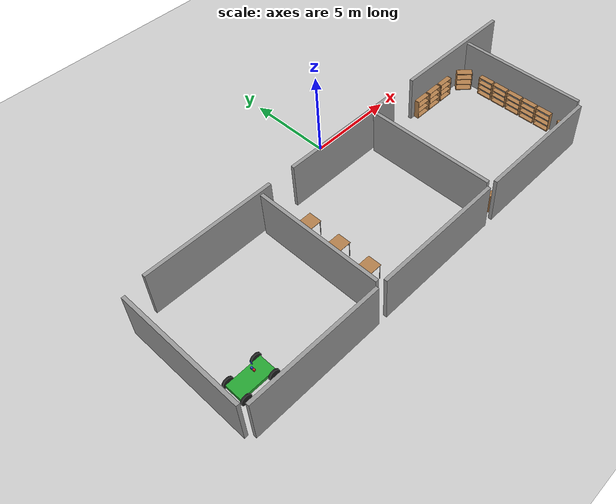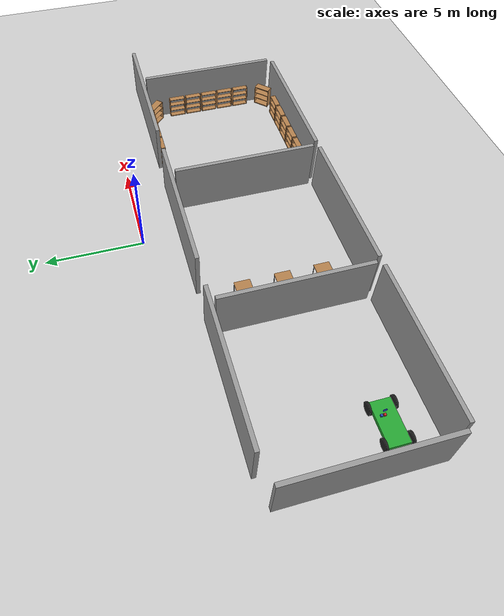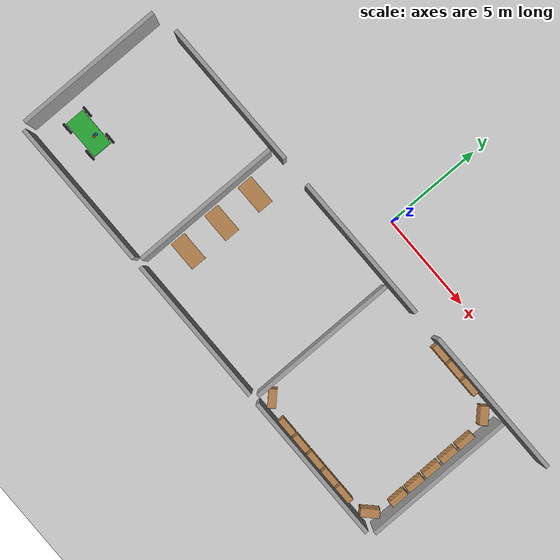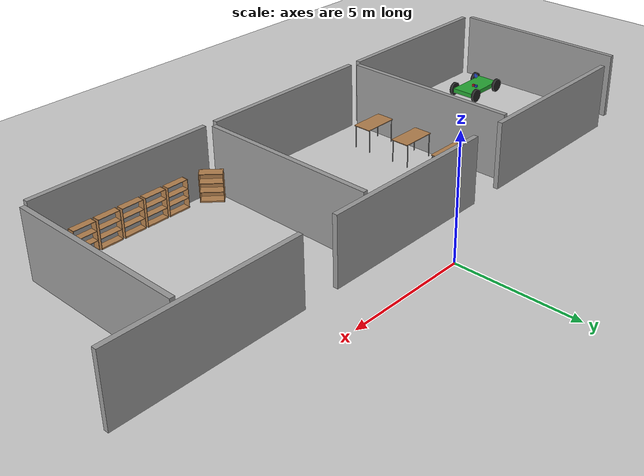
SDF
<sdf version="1.4">
 <world name="default">
  <light name="sun" type="directional">
   <pose>0 0 10 0 -0 0</pose>
   <diffuse>0.8 0.8 0.8 1</diffuse>
   <specular>0.2 0.2 0.2 1</specular>
   <attenuation>
    <range>1000</range>
    <constant>0.9</constant>
    <linear>0.01</linear>
    <quadratic>0.001</quadratic>
   </attenuation>
   <direction>-0.5 0.1 -0.9</direction>
  </light>
  <model name="ground_plane">
   <static>1</static>
   <link name="link">
    <collision name="collision">
     <geometry><plane><normal>0 0 1</normal><size>100 100</size></plane></geometry>
     <surface><friction><ode><mu>100</mu><mu2>50</mu2></ode></friction></surface>
    </collision>
    <visual name="visual">
     <cast_shadows>0</cast_shadows>
     <geometry><plane><normal>0 0 1</normal><size>100 100</size></plane></geometry>
     <material>
      <script><uri>file://media/materials/scripts/gazebo.material</uri><name>Gazebo/Grey</name></script>
     </material>
    </visual>
    <velocity_decay><linear>0</linear><angular>0</angular></velocity_decay>
   </link>
  </model>
  <physics type="ode">
   <max_step_size>0.001</max_step_size>
   <real_time_factor>1</real_time_factor>
   <real_time_update_rate>1000</real_time_update_rate>
   <gravity>0 0 -9.8</gravity>
  </physics>
  <scene><ambient>0.4 0.4 0.4 1</ambient><background>0.7 0.7 0.7 1</background><shadows>1</shadows></scene>
  <spherical_coordinates>
   <surface_model>EARTH_WGS84</surface_model>
   <latitude_deg>0</latitude_deg>
   <longitude_deg>0</longitude_deg>
   <elevation>0</elevation>
   <heading_deg>0</heading_deg>
  </spherical_coordinates>
  <model name="grey_wall">
   <static>1</static>
   <link name="link">
    <pose>0 0 1.4 0 -0 0</pose>
    <collision name="collision"><geometry><box><size>7.5 0.2 2.8</size></box></geometry></collision>
    <visual name="visual">
     <cast_shadows>0</cast_shadows>
     <geometry><box><size>7.5 0.2 2.8</size></box></geometry>
     <material>
      <script>
       <uri>model://grey_wall/materials/scripts</uri>
       <uri>model://grey_wall/materials/textures</uri>
       <name>vrc/grey_wall</name>
      </script>
     </material>
    </visual>
    <velocity_decay><linear>0</linear><angular>0</angular></velocity_decay>
   </link>
   <pose>-2 -10 0 0 -0 0</pose>
  </model>
  <model name="grey_wall_0">
   <static>1</static>
   <link name="link">
    <pose>0 0 1.4 0 -0 0</pose>
    <collision name="collision"><geometry><box><size>7.5 0.2 2.8</size></box></geometry></collision>
    <visual name="visual">
     <cast_shadows>0</cast_shadows>
     <geometry><box><size>7.5 0.2 2.8</size></box></geometry>
     <material>
      <script>
       <uri>model://grey_wall/materials/scripts</uri>
       <uri>model://grey_wall/materials/textures</uri>
       <name>vrc/grey_wall</name>
      </script>
     </material>
    </visual>
    <velocity_decay><linear>0</linear><angular>0</angular></velocity_decay>
   </link>
   <pose>6 -10 0 0 -0 0</pose>
  </model>
  <model name="grey_wall_1">
   <static>1</static>
   <link name="link">
    <pose>0 0 1.4 0 -0 0</pose>
    <collision name="collision"><geometry><box><size>7.5 0.2 2.8</size></box></geometry></collision>
    <visual name="visual">
     <cast_shadows>0</cast_shadows>
     <geometry><box><size>7.5 0.2 2.8</size></box></geometry>
     <material>
      <script>
       <uri>model://grey_wall/materials/scripts</uri>
       <uri>model://grey_wall/materials/textures</uri>
       <name>vrc/grey_wall</name>
      </script>
     </material>
    </visual>
    <velocity_decay><linear>0</linear><angular>0</angular></velocity_decay>
   </link>
   <pose>2 -6 0 0 0 -1.5708</pose>
  </model>
  <model name="grey_wall_2">
   <static>1</static>
   <link name="link">
    <pose>0 0 1.4 0 -0 0</pose>
    <collision name="collision"><geometry><box><size>7.5 0.2 2.8</size></box></geometry></collision>
    <visual name="visual">
     <cast_shadows>0</cast_shadows>
     <geometry><box><size>7.5 0.2 2.8</size></box></geometry>
     <material>
      <script>
       <uri>model://grey_wall/materials/scripts</uri>
       <uri>model://grey_wall/materials/textures</uri>
       <name>vrc/grey_wall</name>
      </script>
     </material>
    </visual>
    <velocity_decay><linear>0</linear><angular>0</angular></velocity_decay>
   </link>
   <pose>9 -2 0 0 -0 0</pose>
  </model>
  <model name="grey_wall_3">
   <static>1</static>
   <link name="link">
    <pose>0 0 1.4 0 -0 0</pose>
    <collision name="collision"><geometry><box><size>7.5 0.2 2.8</size></box></geometry></collision>
    <visual name="visual">
     <cast_shadows>0</cast_shadows>
     <geometry><box><size>7.5 0.2 2.8</size></box></geometry>
     <material>
      <script>
       <uri>model://grey_wall/materials/scripts</uri>
       <uri>model://grey_wall/materials/textures</uri>
       <name>vrc/grey_wall</name>
      </script>
     </material>
    </visual>
    <velocity_decay><linear>0</linear><angular>0</angular></velocity_decay>
   </link>
   <pose>10 -6 0 0 0 -1.5708</pose>
  </model>
  <model name="grey_wall_4">
   <static>1</static>
   <link name="link">
    <pose>0 0 1.4 0 -0 0</pose>
    <collision name="collision"><geometry><box><size>7.5 0.2 2.8</size></box></geometry></collision>
    <visual name="visual">
     <cast_shadows>0</cast_shadows>
     <geometry><box><size>7.5 0.2 2.8</size></box></geometry>
     <material>
      <script>
       <uri>model://grey_wall/materials/scripts</uri>
       <uri>model://grey_wall/materials/textures</uri>
       <name>vrc/grey_wall</name>
      </script>
     </material>
    </visual>
    <velocity_decay><linear>0</linear><angular>0</angular></velocity_decay>
   </link>
   <pose>0 -2 0 0 -0 0</pose>
  </model>
  <model name="grey_wall_5">
   <static>1</static>
   <link name="link">
    <pose>0 0 1.4 0 -0 0</pose>
    <collision name="collision"><geometry><box><size>7.5 0.2 2.8</size></box></geometry></collision>
    <visual name="visual">
     <cast_shadows>0</cast_shadows>
     <geometry><box><size>7.5 0.2 2.8</size></box></geometry>
     <material>
      <script>
       <uri>model://grey_wall/materials/scripts</uri>
       <uri>model://grey_wall/materials/textures</uri>
       <name>vrc/grey_wall</name>
      </script>
     </material>
    </visual>
    <velocity_decay><linear>0</linear><angular>0</angular></velocity_decay>
   </link>
   <pose>-10 -10 0 0 -0 0</pose>
  </model>
  <model name="grey_wall_6">
   <static>1</static>
   <link name="link">
    <pose>0 0 1.4 0 -0 0</pose>
    <collision name="collision"><geometry><box><size>7.5 0.2 2.8</size></box></geometry></collision>
    <visual name="visual">
     <cast_shadows>0</cast_shadows>
     <geometry><box><size>7.5 0.2 2.8</size></box></geometry>
     <material>
      <script>
       <uri>model://grey_wall/materials/scripts</uri>
       <uri>model://grey_wall/materials/textures</uri>
       <name>vrc/grey_wall</name>
      </script>
     </material>
    </visual>
    <velocity_decay><linear>0</linear><angular>0</angular></velocity_decay>
   </link>
   <pose>-6 -6 0 0 0 -1.5708</pose>
  </model>
  <model name="grey_wall_7">
   <static>1</static>
   <link name="link">
    <pose>0 0 1.4 0 -0 0</pose>
    <collision name="collision"><geometry><box><size>7.5 0.2 2.8</size></box></geometry></collision>
    <visual name="visual">
     <cast_shadows>0</cast_shadows>
     <geometry><box><size>7.5 0.2 2.8</size></box></geometry>
     <material>
      <script>
       <uri>model://grey_wall/materials/scripts</uri>
       <uri>model://grey_wall/materials/textures</uri>
       <name>vrc/grey_wall</name>
      </script>
     </material>
    </visual>
    <velocity_decay><linear>0</linear><angular>0</angular></velocity_decay>
   </link>
   <pose>-9 -2 0 0 -0 0</pose>
  </model>
  <model name="grey_wall_8">
   <static>1</static>
   <link name="link">
    <pose>0 0 1.4 0 -0 0</pose>
    <collision name="collision"><geometry><box><size>7.5 0.2 2.8</size></box></geometry></collision>
    <visual name="visual">
     <cast_shadows>0</cast_shadows>
     <geometry><box><size>7.5 0.2 2.8</size></box></geometry>
     <material>
      <script>
       <uri>model://grey_wall/materials/scripts</uri>
       <uri>model://grey_wall/materials/textures</uri>
       <name>vrc/grey_wall</name>
      </script>
     </material>
    </visual>
    <velocity_decay><linear>0</linear><angular>0</angular></velocity_decay>
   </link>
   <pose>-14 -6 0 0 0 -1.5708</pose>
  </model>
  <model name="bookshelf">
   <static>1</static>
   <link name="link">
    <inertial><mass>1</mass></inertial>
    <collision name="back">
     <pose>0 0.005 0.6 0 -0 0</pose>
     <geometry><box><size>0.9 0.01 1.2</size></box></geometry>
    </collision>
    <visual name="visual1">
     <pose>0 0.005 0.6 0 -0 0</pose>
     <geometry><box><size>0.9 0.01 1.2</size></box></geometry>
     <material>
      <script><uri>file://media/materials/scripts/gazebo.material</uri><name>Gazebo/Wood</name></script>
     </material>
    </visual>
    <collision name="left_side">
     <pose>0.45 -0.195 0.6 0 -0 0</pose>
     <geometry><box><size>0.02 0.4 1.2</size></box></geometry>
    </collision>
    <visual name="visual2">
     <pose>0.45 -0.195 0.6 0 -0 0</pose>
     <geometry><box><size>0.02 0.4 1.2</size></box></geometry>
     <material>
      <script><uri>file://media/materials/scripts/gazebo.material</uri><name>Gazebo/Wood</name></script>
     </material>
    </visual>
    <collision name="right_side">
     <pose>-0.45 -0.195 0.6 0 -0 0</pose>
     <geometry><box><size>0.02 0.4 1.2</size></box></geometry>
    </collision>
    <visual name="visual3">
     <pose>-0.45 -0.195 0.6 0 -0 0</pose>
     <geometry><box><size>0.02 0.4 1.2</size></box></geometry>
     <material>
      <script><uri>file://media/materials/scripts/gazebo.material</uri><name>Gazebo/Wood</name></script>
     </material>
    </visual>
    <collision name="bottom">
     <pose>0 -0.195 0.03 0 -0 0</pose>
     <geometry><box><size>0.88 0.4 0.06</size></box></geometry>
    </collision>
    <visual name="visual4">
     <pose>0 -0.195 0.03 0 -0 0</pose>
     <geometry><box><size>0.88 0.4 0.06</size></box></geometry>
     <material>
      <script><uri>file://media/materials/scripts/gazebo.material</uri><name>Gazebo/Wood</name></script>
     </material>
    </visual>
    <collision name="top">
     <pose>0 -0.195 1.19 0 -0 0</pose>
     <geometry><box><size>0.88 0.4 0.02</size></box></geometry>
    </collision>
    <visual name="visual5">
     <pose>0 -0.195 1.19 0 -0 0</pose>
     <geometry><box><size>0.88 0.4 0.02</size></box></geometry>
     <material>
      <script><uri>file://media/materials/scripts/gazebo.material</uri><name>Gazebo/Wood</name></script>
     </material>
    </visual>
    <collision name="low_shelf">
     <pose>0 -0.195 0.43 0 -0 0</pose>
     <geometry><box><size>0.88 0.4 0.02</size></box></geometry>
    </collision>
    <visual name="visual6">
     <pose>0 -0.195 0.43 0 -0 0</pose>
     <geometry><box><size>0.88 0.4 0.02</size></box></geometry>
     <material>
      <script><uri>file://media/materials/scripts/gazebo.material</uri><name>Gazebo/Wood</name></script>
     </material>
    </visual>
    <collision name="high_shelf">
     <pose>0 -0.195 0.8 0 -0 0</pose>
     <geometry><box><size>0.88 0.4 0.02</size></box></geometry>
    </collision>
    <visual name="visual7">
     <pose>0 -0.195 0.8 0 -0 0</pose>
     <geometry><box><size>0.88 0.4 0.02</size></box></geometry>
     <material>
      <script><uri>file://media/materials/scripts/gazebo.material</uri><name>Gazebo/Wood</name></script>
     </material>
    </visual>
    <velocity_decay><linear>0</linear><angular>0</angular></velocity_decay>
   </link>
   <pose>2.43808 -9.56157 0 0 -0 2.35619</pose>
  </model>
  <model name="bookshelf_0">
   <static>1</static>
   <link name="link">
    <inertial><mass>1</mass></inertial>
    <collision name="back">
     <pose>0 0.005 0.6 0 -0 0</pose>
     <geometry><box><size>0.9 0.01 1.2</size></box></geometry>
    </collision>
    <visual name="visual1">
     <pose>0 0.005 0.6 0 -0 0</pose>
     <geometry><box><size>0.9 0.01 1.2</size></box></geometry>
     <material>
      <script><uri>file://media/materials/scripts/gazebo.material</uri><name>Gazebo/Wood</name></script>
     </material>
    </visual>
    <collision name="left_side">
     <pose>0.45 -0.195 0.6 0 -0 0</pose>
     <geometry><box><size>0.02 0.4 1.2</size></box></geometry>
    </collision>
    <visual name="visual2">
     <pose>0.45 -0.195 0.6 0 -0 0</pose>
     <geometry><box><size>0.02 0.4 1.2</size></box></geometry>
     <material>
      <script><uri>file://media/materials/scripts/gazebo.material</uri><name>Gazebo/Wood</name></script>
     </material>
    </visual>
    <collision name="right_side">
     <pose>-0.45 -0.195 0.6 0 -0 0</pose>
     <geometry><box><size>0.02 0.4 1.2</size></box></geometry>
    </collision>
    <visual name="visual3">
     <pose>-0.45 -0.195 0.6 0 -0 0</pose>
     <geometry><box><size>0.02 0.4 1.2</size></box></geometry>
     <material>
      <script><uri>file://media/materials/scripts/gazebo.material</uri><name>Gazebo/Wood</name></script>
     </material>
    </visual>
    <collision name="bottom">
     <pose>0 -0.195 0.03 0 -0 0</pose>
     <geometry><box><size>0.88 0.4 0.06</size></box></geometry>
    </collision>
    <visual name="visual4">
     <pose>0 -0.195 0.03 0 -0 0</pose>
     <geometry><box><size>0.88 0.4 0.06</size></box></geometry>
     <material>
      <script><uri>file://media/materials/scripts/gazebo.material</uri><name>Gazebo/Wood</name></script>
     </material>
    </visual>
    <collision name="top">
     <pose>0 -0.195 1.19 0 -0 0</pose>
     <geometry><box><size>0.88 0.4 0.02</size></box></geometry>
    </collision>
    <visual name="visual5">
     <pose>0 -0.195 1.19 0 -0 0</pose>
     <geometry><box><size>0.88 0.4 0.02</size></box></geometry>
     <material>
      <script><uri>file://media/materials/scripts/gazebo.material</uri><name>Gazebo/Wood</name></script>
     </material>
    </visual>
    <collision name="low_shelf">
     <pose>0 -0.195 0.43 0 -0 0</pose>
     <geometry><box><size>0.88 0.4 0.02</size></box></geometry>
    </collision>
    <visual name="visual6">
     <pose>0 -0.195 0.43 0 -0 0</pose>
     <geometry><box><size>0.88 0.4 0.02</size></box></geometry>
     <material>
      <script><uri>file://media/materials/scripts/gazebo.material</uri><name>Gazebo/Wood</name></script>
     </material>
    </visual>
    <collision name="high_shelf">
     <pose>0 -0.195 0.8 0 -0 0</pose>
     <geometry><box><size>0.88 0.4 0.02</size></box></geometry>
    </collision>
    <visual name="visual7">
     <pose>0 -0.195 0.8 0 -0 0</pose>
     <geometry><box><size>0.88 0.4 0.02</size></box></geometry>
     <material>
      <script><uri>file://media/materials/scripts/gazebo.material</uri><name>Gazebo/Wood</name></script>
     </material>
    </visual>
    <velocity_decay><linear>0</linear><angular>0</angular></velocity_decay>
   </link>
   <pose>4 -10 0 0 0 -3.14159</pose>
  </model>
  <model name="bookshelf_1">
   <static>1</static>
   <link name="link">
    <inertial><mass>1</mass></inertial>
    <collision name="back">
     <pose>0 0.005 0.6 0 -0 0</pose>
     <geometry><box><size>0.9 0.01 1.2</size></box></geometry>
    </collision>
    <visual name="visual1">
     <pose>0 0.005 0.6 0 -0 0</pose>
     <geometry><box><size>0.9 0.01 1.2</size></box></geometry>
     <material>
      <script><uri>file://media/materials/scripts/gazebo.material</uri><name>Gazebo/Wood</name></script>
     </material>
    </visual>
    <collision name="left_side">
     <pose>0.45 -0.195 0.6 0 -0 0</pose>
     <geometry><box><size>0.02 0.4 1.2</size></box></geometry>
    </collision>
    <visual name="visual2">
     <pose>0.45 -0.195 0.6 0 -0 0</pose>
     <geometry><box><size>0.02 0.4 1.2</size></box></geometry>
     <material>
      <script><uri>file://media/materials/scripts/gazebo.material</uri><name>Gazebo/Wood</name></script>
     </material>
    </visual>
    <collision name="right_side">
     <pose>-0.45 -0.195 0.6 0 -0 0</pose>
     <geometry><box><size>0.02 0.4 1.2</size></box></geometry>
    </collision>
    <visual name="visual3">
     <pose>-0.45 -0.195 0.6 0 -0 0</pose>
     <geometry><box><size>0.02 0.4 1.2</size></box></geometry>
     <material>
      <script><uri>file://media/materials/scripts/gazebo.material</uri><name>Gazebo/Wood</name></script>
     </material>
    </visual>
    <collision name="bottom">
     <pose>0 -0.195 0.03 0 -0 0</pose>
     <geometry><box><size>0.88 0.4 0.06</size></box></geometry>
    </collision>
    <visual name="visual4">
     <pose>0 -0.195 0.03 0 -0 0</pose>
     <geometry><box><size>0.88 0.4 0.06</size></box></geometry>
     <material>
      <script><uri>file://media/materials/scripts/gazebo.material</uri><name>Gazebo/Wood</name></script>
     </material>
    </visual>
    <collision name="top">
     <pose>0 -0.195 1.19 0 -0 0</pose>
     <geometry><box><size>0.88 0.4 0.02</size></box></geometry>
    </collision>
    <visual name="visual5">
     <pose>0 -0.195 1.19 0 -0 0</pose>
     <geometry><box><size>0.88 0.4 0.02</size></box></geometry>
     <material>
      <script><uri>file://media/materials/scripts/gazebo.material</uri><name>Gazebo/Wood</name></script>
     </material>
    </visual>
    <collision name="low_shelf">
     <pose>0 -0.195 0.43 0 -0 0</pose>
     <geometry><box><size>0.88 0.4 0.02</size></box></geometry>
    </collision>
    <visual name="visual6">
     <pose>0 -0.195 0.43 0 -0 0</pose>
     <geometry><box><size>0.88 0.4 0.02</size></box></geometry>
     <material>
      <script><uri>file://media/materials/scripts/gazebo.material</uri><name>Gazebo/Wood</name></script>
     </material>
    </visual>
    <collision name="high_shelf">
     <pose>0 -0.195 0.8 0 -0 0</pose>
     <geometry><box><size>0.88 0.4 0.02</size></box></geometry>
    </collision>
    <visual name="visual7">
     <pose>0 -0.195 0.8 0 -0 0</pose>
     <geometry><box><size>0.88 0.4 0.02</size></box></geometry>
     <material>
      <script><uri>file://media/materials/scripts/gazebo.material</uri><name>Gazebo/Wood</name></script>
     </material>
    </visual>
    <velocity_decay><linear>0</linear><angular>0</angular></velocity_decay>
   </link>
   <pose>5 -10 0 0 -0 3.14159</pose>
  </model>
  <model name="table">
   <static>1</static>
   <link name="link">
    <collision name="surface">
     <pose>0 0 1 0 -0 0</pose>
     <geometry><box><size>1.5 0.8 0.03</size></box></geometry>
     <surface><friction><ode><mu>0.6</mu><mu2>0.6</mu2></ode></friction></surface>
    </collision>
    <visual name="visual1">
     <pose>0 0 1 0 -0 0</pose>
     <geometry><box><size>1.5 0.8 0.03</size></box></geometry>
     <material>
      <script><uri>file://media/materials/scripts/gazebo.material</uri><name>Gazebo/Wood</name></script>
     </material>
    </visual>
    <collision name="front_left_leg">
     <pose>0.68 0.38 0.5 0 -0 0</pose>
     <geometry><cylinder><radius>0.02</radius><length>1</length></cylinder></geometry>
    </collision>
    <visual name="front_left_leg">
     <pose>0.68 0.38 0.5 0 -0 0</pose>
     <geometry><cylinder><radius>0.02</radius><length>1</length></cylinder></geometry>
     <material>
      <script><uri>file://media/materials/scripts/gazebo.material</uri><name>Gazebo/Grey</name></script>
     </material>
    </visual>
    <collision name="front_right_leg">
     <pose>0.68 -0.38 0.5 0 -0 0</pose>
     <geometry><cylinder><radius>0.02</radius><length>1</length></cylinder></geometry>
    </collision>
    <visual name="front_right_leg">
     <pose>0.68 -0.38 0.5 0 -0 0</pose>
     <geometry><cylinder><radius>0.02</radius><length>1</length></cylinder></geometry>
     <material>
      <script><uri>file://media/materials/scripts/gazebo.material</uri><name>Gazebo/Grey</name></script>
     </material>
    </visual>
    <collision name="back_right_leg">
     <pose>-0.68 -0.38 0.5 0 -0 0</pose>
     <geometry><cylinder><radius>0.02</radius><length>1</length></cylinder></geometry>
    </collision>
    <visual name="back_right_leg">
     <pose>-0.68 -0.38 0.5 0 -0 0</pose>
     <geometry><cylinder><radius>0.02</radius><length>1</length></cylinder></geometry>
     <material>
      <script><uri>file://media/materials/scripts/gazebo.material</uri><name>Gazebo/Grey</name></script>
     </material>
    </visual>
    <collision name="back_left_leg">
     <pose>-0.68 0.38 0.5 0 -0 0</pose>
     <geometry><cylinder><radius>0.02</radius><length>1</length></cylinder></geometry>
    </collision>
    <visual name="back_left_leg">
     <pose>-0.68 0.38 0.5 0 -0 0</pose>
     <geometry><cylinder><radius>0.02</radius><length>1</length></cylinder></geometry>
     <material>
      <script><uri>file://media/materials/scripts/gazebo.material</uri><name>Gazebo/Grey</name></script>
     </material>
    </visual>
    <velocity_decay><linear>0</linear><angular>0</angular></velocity_decay>
   </link>
   <pose>-5 -8 0 0 -0 0</pose>
  </model>
  <model name="bookshelf_2">
   <static>1</static>
   <link name="link">
    <inertial><mass>1</mass></inertial>
    <collision name="back">
     <pose>0 0.005 0.6 0 -0 0</pose>
     <geometry><box><size>0.9 0.01 1.2</size></box></geometry>
    </collision>
    <visual name="visual1">
     <pose>0 0.005 0.6 0 -0 0</pose>
     <geometry><box><size>0.9 0.01 1.2</size></box></geometry>
     <material>
      <script><uri>file://media/materials/scripts/gazebo.material</uri><name>Gazebo/Wood</name></script>
     </material>
    </visual>
    <collision name="left_side">
     <pose>0.45 -0.195 0.6 0 -0 0</pose>
     <geometry><box><size>0.02 0.4 1.2</size></box></geometry>
    </collision>
    <visual name="visual2">
     <pose>0.45 -0.195 0.6 0 -0 0</pose>
     <geometry><box><size>0.02 0.4 1.2</size></box></geometry>
     <material>
      <script><uri>file://media/materials/scripts/gazebo.material</uri><name>Gazebo/Wood</name></script>
     </material>
    </visual>
    <collision name="right_side">
     <pose>-0.45 -0.195 0.6 0 -0 0</pose>
     <geometry><box><size>0.02 0.4 1.2</size></box></geometry>
    </collision>
    <visual name="visual3">
     <pose>-0.45 -0.195 0.6 0 -0 0</pose>
     <geometry><box><size>0.02 0.4 1.2</size></box></geometry>
     <material>
      <script><uri>file://media/materials/scripts/gazebo.material</uri><name>Gazebo/Wood</name></script>
     </material>
    </visual>
    <collision name="bottom">
     <pose>0 -0.195 0.03 0 -0 0</pose>
     <geometry><box><size>0.88 0.4 0.06</size></box></geometry>
    </collision>
    <visual name="visual4">
     <pose>0 -0.195 0.03 0 -0 0</pose>
     <geometry><box><size>0.88 0.4 0.06</size></box></geometry>
     <material>
      <script><uri>file://media/materials/scripts/gazebo.material</uri><name>Gazebo/Wood</name></script>
     </material>
    </visual>
    <collision name="top">
     <pose>0 -0.195 1.19 0 -0 0</pose>
     <geometry><box><size>0.88 0.4 0.02</size></box></geometry>
    </collision>
    <visual name="visual5">
     <pose>0 -0.195 1.19 0 -0 0</pose>
     <geometry><box><size>0.88 0.4 0.02</size></box></geometry>
     <material>
      <script><uri>file://media/materials/scripts/gazebo.material</uri><name>Gazebo/Wood</name></script>
     </material>
    </visual>
    <collision name="low_shelf">
     <pose>0 -0.195 0.43 0 -0 0</pose>
     <geometry><box><size>0.88 0.4 0.02</size></box></geometry>
    </collision>
    <visual name="visual6">
     <pose>0 -0.195 0.43 0 -0 0</pose>
     <geometry><box><size>0.88 0.4 0.02</size></box></geometry>
     <material>
      <script><uri>file://media/materials/scripts/gazebo.material</uri><name>Gazebo/Wood</name></script>
     </material>
    </visual>
    <collision name="high_shelf">
     <pose>0 -0.195 0.8 0 -0 0</pose>
     <geometry><box><size>0.88 0.4 0.02</size></box></geometry>
    </collision>
    <visual name="visual7">
     <pose>0 -0.195 0.8 0 -0 0</pose>
     <geometry><box><size>0.88 0.4 0.02</size></box></geometry>
     <material>
      <script><uri>file://media/materials/scripts/gazebo.material</uri><name>Gazebo/Wood</name></script>
     </material>
    </visual>
    <velocity_decay><linear>0</linear><angular>0</angular></velocity_decay>
   </link>
   <pose>6 -2 0 0 -0 0</pose>
  </model>
  <model name="bookshelf_3">
   <static>1</static>
   <link name="link">
    <inertial><mass>1</mass></inertial>
    <collision name="back">
     <pose>0 0.005 0.6 0 -0 0</pose>
     <geometry><box><size>0.9 0.01 1.2</size></box></geometry>
    </collision>
    <visual name="visual1">
     <pose>0 0.005 0.6 0 -0 0</pose>
     <geometry><box><size>0.9 0.01 1.2</size></box></geometry>
     <material>
      <script><uri>file://media/materials/scripts/gazebo.material</uri><name>Gazebo/Wood</name></script>
     </material>
    </visual>
    <collision name="left_side">
     <pose>0.45 -0.195 0.6 0 -0 0</pose>
     <geometry><box><size>0.02 0.4 1.2</size></box></geometry>
    </collision>
    <visual name="visual2">
     <pose>0.45 -0.195 0.6 0 -0 0</pose>
     <geometry><box><size>0.02 0.4 1.2</size></box></geometry>
     <material>
      <script><uri>file://media/materials/scripts/gazebo.material</uri><name>Gazebo/Wood</name></script>
     </material>
    </visual>
    <collision name="right_side">
     <pose>-0.45 -0.195 0.6 0 -0 0</pose>
     <geometry><box><size>0.02 0.4 1.2</size></box></geometry>
    </collision>
    <visual name="visual3">
     <pose>-0.45 -0.195 0.6 0 -0 0</pose>
     <geometry><box><size>0.02 0.4 1.2</size></box></geometry>
     <material>
      <script><uri>file://media/materials/scripts/gazebo.material</uri><name>Gazebo/Wood</name></script>
     </material>
    </visual>
    <collision name="bottom">
     <pose>0 -0.195 0.03 0 -0 0</pose>
     <geometry><box><size>0.88 0.4 0.06</size></box></geometry>
    </collision>
    <visual name="visual4">
     <pose>0 -0.195 0.03 0 -0 0</pose>
     <geometry><box><size>0.88 0.4 0.06</size></box></geometry>
     <material>
      <script><uri>file://media/materials/scripts/gazebo.material</uri><name>Gazebo/Wood</name></script>
     </material>
    </visual>
    <collision name="top">
     <pose>0 -0.195 1.19 0 -0 0</pose>
     <geometry><box><size>0.88 0.4 0.02</size></box></geometry>
    </collision>
    <visual name="visual5">
     <pose>0 -0.195 1.19 0 -0 0</pose>
     <geometry><box><size>0.88 0.4 0.02</size></box></geometry>
     <material>
      <script><uri>file://media/materials/scripts/gazebo.material</uri><name>Gazebo/Wood</name></script>
     </material>
    </visual>
    <collision name="low_shelf">
     <pose>0 -0.195 0.43 0 -0 0</pose>
     <geometry><box><size>0.88 0.4 0.02</size></box></geometry>
    </collision>
    <visual name="visual6">
     <pose>0 -0.195 0.43 0 -0 0</pose>
     <geometry><box><size>0.88 0.4 0.02</size></box></geometry>
     <material>
      <script><uri>file://media/materials/scripts/gazebo.material</uri><name>Gazebo/Wood</name></script>
     </material>
    </visual>
    <collision name="high_shelf">
     <pose>0 -0.195 0.8 0 -0 0</pose>
     <geometry><box><size>0.88 0.4 0.02</size></box></geometry>
    </collision>
    <visual name="visual7">
     <pose>0 -0.195 0.8 0 -0 0</pose>
     <geometry><box><size>0.88 0.4 0.02</size></box></geometry>
     <material>
      <script><uri>file://media/materials/scripts/gazebo.material</uri><name>Gazebo/Wood</name></script>
     </material>
    </visual>
    <velocity_decay><linear>0</linear><angular>0</angular></velocity_decay>
   </link>
   <pose>6 -10 0 0 0 -3.14159</pose>
  </model>
  <model name="bookshelf_4">
   <static>1</static>
   <link name="link">
    <inertial><mass>1</mass></inertial>
    <collision name="back">
     <pose>0 0.005 0.6 0 -0 0</pose>
     <geometry><box><size>0.9 0.01 1.2</size></box></geometry>
    </collision>
    <visual name="visual1">
     <pose>0 0.005 0.6 0 -0 0</pose>
     <geometry><box><size>0.9 0.01 1.2</size></box></geometry>
     <material>
      <script><uri>file://media/materials/scripts/gazebo.material</uri><name>Gazebo/Wood</name></script>
     </material>
    </visual>
    <collision name="left_side">
     <pose>0.45 -0.195 0.6 0 -0 0</pose>
     <geometry><box><size>0.02 0.4 1.2</size></box></geometry>
    </collision>
    <visual name="visual2">
     <pose>0.45 -0.195 0.6 0 -0 0</pose>
     <geometry><box><size>0.02 0.4 1.2</size></box></geometry>
     <material>
      <script><uri>file://media/materials/scripts/gazebo.material</uri><name>Gazebo/Wood</name></script>
     </material>
    </visual>
    <collision name="right_side">
     <pose>-0.45 -0.195 0.6 0 -0 0</pose>
     <geometry><box><size>0.02 0.4 1.2</size></box></geometry>
    </collision>
    <visual name="visual3">
     <pose>-0.45 -0.195 0.6 0 -0 0</pose>
     <geometry><box><size>0.02 0.4 1.2</size></box></geometry>
     <material>
      <script><uri>file://media/materials/scripts/gazebo.material</uri><name>Gazebo/Wood</name></script>
     </material>
    </visual>
    <collision name="bottom">
     <pose>0 -0.195 0.03 0 -0 0</pose>
     <geometry><box><size>0.88 0.4 0.06</size></box></geometry>
    </collision>
    <visual name="visual4">
     <pose>0 -0.195 0.03 0 -0 0</pose>
     <geometry><box><size>0.88 0.4 0.06</size></box></geometry>
     <material>
      <script><uri>file://media/materials/scripts/gazebo.material</uri><name>Gazebo/Wood</name></script>
     </material>
    </visual>
    <collision name="top">
     <pose>0 -0.195 1.19 0 -0 0</pose>
     <geometry><box><size>0.88 0.4 0.02</size></box></geometry>
    </collision>
    <visual name="visual5">
     <pose>0 -0.195 1.19 0 -0 0</pose>
     <geometry><box><size>0.88 0.4 0.02</size></box></geometry>
     <material>
      <script><uri>file://media/materials/scripts/gazebo.material</uri><name>Gazebo/Wood</name></script>
     </material>
    </visual>
    <collision name="low_shelf">
     <pose>0 -0.195 0.43 0 -0 0</pose>
     <geometry><box><size>0.88 0.4 0.02</size></box></geometry>
    </collision>
    <visual name="visual6">
     <pose>0 -0.195 0.43 0 -0 0</pose>
     <geometry><box><size>0.88 0.4 0.02</size></box></geometry>
     <material>
      <script><uri>file://media/materials/scripts/gazebo.material</uri><name>Gazebo/Wood</name></script>
     </material>
    </visual>
    <collision name="high_shelf">
     <pose>0 -0.195 0.8 0 -0 0</pose>
     <geometry><box><size>0.88 0.4 0.02</size></box></geometry>
    </collision>
    <visual name="visual7">
     <pose>0 -0.195 0.8 0 -0 0</pose>
     <geometry><box><size>0.88 0.4 0.02</size></box></geometry>
     <material>
      <script><uri>file://media/materials/scripts/gazebo.material</uri><name>Gazebo/Wood</name></script>
     </material>
    </visual>
    <velocity_decay><linear>0</linear><angular>0</angular></velocity_decay>
   </link>
   <pose>9.55807 -9.56504 0 0 0 -2.35619</pose>
  </model>
  <model name="bookshelf_5">
   <static>1</static>
   <link name="link">
    <inertial><mass>1</mass></inertial>
    <collision name="back">
     <pose>0 0.005 0.6 0 -0 0</pose>
     <geometry><box><size>0.9 0.01 1.2</size></box></geometry>
    </collision>
    <visual name="visual1">
     <pose>0 0.005 0.6 0 -0 0</pose>
     <geometry><box><size>0.9 0.01 1.2</size></box></geometry>
     <material>
      <script><uri>file://media/materials/scripts/gazebo.material</uri><name>Gazebo/Wood</name></script>
     </material>
    </visual>
    <collision name="left_side">
     <pose>0.45 -0.195 0.6 0 -0 0</pose>
     <geometry><box><size>0.02 0.4 1.2</size></box></geometry>
    </collision>
    <visual name="visual2">
     <pose>0.45 -0.195 0.6 0 -0 0</pose>
     <geometry><box><size>0.02 0.4 1.2</size></box></geometry>
     <material>
      <script><uri>file://media/materials/scripts/gazebo.material</uri><name>Gazebo/Wood</name></script>
     </material>
    </visual>
    <collision name="right_side">
     <pose>-0.45 -0.195 0.6 0 -0 0</pose>
     <geometry><box><size>0.02 0.4 1.2</size></box></geometry>
    </collision>
    <visual name="visual3">
     <pose>-0.45 -0.195 0.6 0 -0 0</pose>
     <geometry><box><size>0.02 0.4 1.2</size></box></geometry>
     <material>
      <script><uri>file://media/materials/scripts/gazebo.material</uri><name>Gazebo/Wood</name></script>
     </material>
    </visual>
    <collision name="bottom">
     <pose>0 -0.195 0.03 0 -0 0</pose>
     <geometry><box><size>0.88 0.4 0.06</size></box></geometry>
    </collision>
    <visual name="visual4">
     <pose>0 -0.195 0.03 0 -0 0</pose>
     <geometry><box><size>0.88 0.4 0.06</size></box></geometry>
     <material>
      <script><uri>file://media/materials/scripts/gazebo.material</uri><name>Gazebo/Wood</name></script>
     </material>
    </visual>
    <collision name="top">
     <pose>0 -0.195 1.19 0 -0 0</pose>
     <geometry><box><size>0.88 0.4 0.02</size></box></geometry>
    </collision>
    <visual name="visual5">
     <pose>0 -0.195 1.19 0 -0 0</pose>
     <geometry><box><size>0.88 0.4 0.02</size></box></geometry>
     <material>
      <script><uri>file://media/materials/scripts/gazebo.material</uri><name>Gazebo/Wood</name></script>
     </material>
    </visual>
    <collision name="low_shelf">
     <pose>0 -0.195 0.43 0 -0 0</pose>
     <geometry><box><size>0.88 0.4 0.02</size></box></geometry>
    </collision>
    <visual name="visual6">
     <pose>0 -0.195 0.43 0 -0 0</pose>
     <geometry><box><size>0.88 0.4 0.02</size></box></geometry>
     <material>
      <script><uri>file://media/materials/scripts/gazebo.material</uri><name>Gazebo/Wood</name></script>
     </material>
    </visual>
    <collision name="high_shelf">
     <pose>0 -0.195 0.8 0 -0 0</pose>
     <geometry><box><size>0.88 0.4 0.02</size></box></geometry>
    </collision>
    <visual name="visual7">
     <pose>0 -0.195 0.8 0 -0 0</pose>
     <geometry><box><size>0.88 0.4 0.02</size></box></geometry>
     <material>
      <script><uri>file://media/materials/scripts/gazebo.material</uri><name>Gazebo/Wood</name></script>
     </material>
    </visual>
    <velocity_decay><linear>0</linear><angular>0</angular></velocity_decay>
   </link>
   <pose>7 -10 0 0 -0 3.14159</pose>
  </model>
  <model name="bookshelf_6">
   <static>1</static>
   <link name="link">
    <inertial><mass>1</mass></inertial>
    <collision name="back">
     <pose>0 0.005 0.6 0 -0 0</pose>
     <geometry><box><size>0.9 0.01 1.2</size></box></geometry>
    </collision>
    <visual name="visual1">
     <pose>0 0.005 0.6 0 -0 0</pose>
     <geometry><box><size>0.9 0.01 1.2</size></box></geometry>
     <material>
      <script><uri>file://media/materials/scripts/gazebo.material</uri><name>Gazebo/Wood</name></script>
     </material>
    </visual>
    <collision name="left_side">
     <pose>0.45 -0.195 0.6 0 -0 0</pose>
     <geometry><box><size>0.02 0.4 1.2</size></box></geometry>
    </collision>
    <visual name="visual2">
     <pose>0.45 -0.195 0.6 0 -0 0</pose>
     <geometry><box><size>0.02 0.4 1.2</size></box></geometry>
     <material>
      <script><uri>file://media/materials/scripts/gazebo.material</uri><name>Gazebo/Wood</name></script>
     </material>
    </visual>
    <collision name="right_side">
     <pose>-0.45 -0.195 0.6 0 -0 0</pose>
     <geometry><box><size>0.02 0.4 1.2</size></box></geometry>
    </collision>
    <visual name="visual3">
     <pose>-0.45 -0.195 0.6 0 -0 0</pose>
     <geometry><box><size>0.02 0.4 1.2</size></box></geometry>
     <material>
      <script><uri>file://media/materials/scripts/gazebo.material</uri><name>Gazebo/Wood</name></script>
     </material>
    </visual>
    <collision name="bottom">
     <pose>0 -0.195 0.03 0 -0 0</pose>
     <geometry><box><size>0.88 0.4 0.06</size></box></geometry>
    </collision>
    <visual name="visual4">
     <pose>0 -0.195 0.03 0 -0 0</pose>
     <geometry><box><size>0.88 0.4 0.06</size></box></geometry>
     <material>
      <script><uri>file://media/materials/scripts/gazebo.material</uri><name>Gazebo/Wood</name></script>
     </material>
    </visual>
    <collision name="top">
     <pose>0 -0.195 1.19 0 -0 0</pose>
     <geometry><box><size>0.88 0.4 0.02</size></box></geometry>
    </collision>
    <visual name="visual5">
     <pose>0 -0.195 1.19 0 -0 0</pose>
     <geometry><box><size>0.88 0.4 0.02</size></box></geometry>
     <material>
      <script><uri>file://media/materials/scripts/gazebo.material</uri><name>Gazebo/Wood</name></script>
     </material>
    </visual>
    <collision name="low_shelf">
     <pose>0 -0.195 0.43 0 -0 0</pose>
     <geometry><box><size>0.88 0.4 0.02</size></box></geometry>
    </collision>
    <visual name="visual6">
     <pose>0 -0.195 0.43 0 -0 0</pose>
     <geometry><box><size>0.88 0.4 0.02</size></box></geometry>
     <material>
      <script><uri>file://media/materials/scripts/gazebo.material</uri><name>Gazebo/Wood</name></script>
     </material>
    </visual>
    <collision name="high_shelf">
     <pose>0 -0.195 0.8 0 -0 0</pose>
     <geometry><box><size>0.88 0.4 0.02</size></box></geometry>
    </collision>
    <visual name="visual7">
     <pose>0 -0.195 0.8 0 -0 0</pose>
     <geometry><box><size>0.88 0.4 0.02</size></box></geometry>
     <material>
      <script><uri>file://media/materials/scripts/gazebo.material</uri><name>Gazebo/Wood</name></script>
     </material>
    </visual>
    <velocity_decay><linear>0</linear><angular>0</angular></velocity_decay>
   </link>
   <pose>8 -10 0 0 -0 3.14159</pose>
  </model>
  <model name="bookshelf_7">
   <static>1</static>
   <link name="link">
    <inertial><mass>1</mass></inertial>
    <collision name="back">
     <pose>0 0.005 0.6 0 -0 0</pose>
     <geometry><box><size>0.9 0.01 1.2</size></box></geometry>
    </collision>
    <visual name="visual1">
     <pose>0 0.005 0.6 0 -0 0</pose>
     <geometry><box><size>0.9 0.01 1.2</size></box></geometry>
     <material>
      <script><uri>file://media/materials/scripts/gazebo.material</uri><name>Gazebo/Wood</name></script>
     </material>
    </visual>
    <collision name="left_side">
     <pose>0.45 -0.195 0.6 0 -0 0</pose>
     <geometry><box><size>0.02 0.4 1.2</size></box></geometry>
    </collision>
    <visual name="visual2">
     <pose>0.45 -0.195 0.6 0 -0 0</pose>
     <geometry><box><size>0.02 0.4 1.2</size></box></geometry>
     <material>
      <script><uri>file://media/materials/scripts/gazebo.material</uri><name>Gazebo/Wood</name></script>
     </material>
    </visual>
    <collision name="right_side">
     <pose>-0.45 -0.195 0.6 0 -0 0</pose>
     <geometry><box><size>0.02 0.4 1.2</size></box></geometry>
    </collision>
    <visual name="visual3">
     <pose>-0.45 -0.195 0.6 0 -0 0</pose>
     <geometry><box><size>0.02 0.4 1.2</size></box></geometry>
     <material>
      <script><uri>file://media/materials/scripts/gazebo.material</uri><name>Gazebo/Wood</name></script>
     </material>
    </visual>
    <collision name="bottom">
     <pose>0 -0.195 0.03 0 -0 0</pose>
     <geometry><box><size>0.88 0.4 0.06</size></box></geometry>
    </collision>
    <visual name="visual4">
     <pose>0 -0.195 0.03 0 -0 0</pose>
     <geometry><box><size>0.88 0.4 0.06</size></box></geometry>
     <material>
      <script><uri>file://media/materials/scripts/gazebo.material</uri><name>Gazebo/Wood</name></script>
     </material>
    </visual>
    <collision name="top">
     <pose>0 -0.195 1.19 0 -0 0</pose>
     <geometry><box><size>0.88 0.4 0.02</size></box></geometry>
    </collision>
    <visual name="visual5">
     <pose>0 -0.195 1.19 0 -0 0</pose>
     <geometry><box><size>0.88 0.4 0.02</size></box></geometry>
     <material>
      <script><uri>file://media/materials/scripts/gazebo.material</uri><name>Gazebo/Wood</name></script>
     </material>
    </visual>
    <collision name="low_shelf">
     <pose>0 -0.195 0.43 0 -0 0</pose>
     <geometry><box><size>0.88 0.4 0.02</size></box></geometry>
    </collision>
    <visual name="visual6">
     <pose>0 -0.195 0.43 0 -0 0</pose>
     <geometry><box><size>0.88 0.4 0.02</size></box></geometry>
     <material>
      <script><uri>file://media/materials/scripts/gazebo.material</uri><name>Gazebo/Wood</name></script>
     </material>
    </visual>
    <collision name="high_shelf">
     <pose>0 -0.195 0.8 0 -0 0</pose>
     <geometry><box><size>0.88 0.4 0.02</size></box></geometry>
    </collision>
    <visual name="visual7">
     <pose>0 -0.195 0.8 0 -0 0</pose>
     <geometry><box><size>0.88 0.4 0.02</size></box></geometry>
     <material>
      <script><uri>file://media/materials/scripts/gazebo.material</uri><name>Gazebo/Wood</name></script>
     </material>
    </visual>
    <velocity_decay><linear>0</linear><angular>0</angular></velocity_decay>
   </link>
   <pose>7 -2 0 0 -0 0</pose>
  </model>
  <model name="bookshelf_8">
   <static>1</static>
   <link name="link">
    <inertial><mass>1</mass></inertial>
    <collision name="back">
     <pose>0 0.005 0.6 0 -0 0</pose>
     <geometry><box><size>0.9 0.01 1.2</size></box></geometry>
    </collision>
    <visual name="visual1">
     <pose>0 0.005 0.6 0 -0 0</pose>
     <geometry><box><size>0.9 0.01 1.2</size></box></geometry>
     <material>
      <script><uri>file://media/materials/scripts/gazebo.material</uri><name>Gazebo/Wood</name></script>
     </material>
    </visual>
    <collision name="left_side">
     <pose>0.45 -0.195 0.6 0 -0 0</pose>
     <geometry><box><size>0.02 0.4 1.2</size></box></geometry>
    </collision>
    <visual name="visual2">
     <pose>0.45 -0.195 0.6 0 -0 0</pose>
     <geometry><box><size>0.02 0.4 1.2</size></box></geometry>
     <material>
      <script><uri>file://media/materials/scripts/gazebo.material</uri><name>Gazebo/Wood</name></script>
     </material>
    </visual>
    <collision name="right_side">
     <pose>-0.45 -0.195 0.6 0 -0 0</pose>
     <geometry><box><size>0.02 0.4 1.2</size></box></geometry>
    </collision>
    <visual name="visual3">
     <pose>-0.45 -0.195 0.6 0 -0 0</pose>
     <geometry><box><size>0.02 0.4 1.2</size></box></geometry>
     <material>
      <script><uri>file://media/materials/scripts/gazebo.material</uri><name>Gazebo/Wood</name></script>
     </material>
    </visual>
    <collision name="bottom">
     <pose>0 -0.195 0.03 0 -0 0</pose>
     <geometry><box><size>0.88 0.4 0.06</size></box></geometry>
    </collision>
    <visual name="visual4">
     <pose>0 -0.195 0.03 0 -0 0</pose>
     <geometry><box><size>0.88 0.4 0.06</size></box></geometry>
     <material>
      <script><uri>file://media/materials/scripts/gazebo.material</uri><name>Gazebo/Wood</name></script>
     </material>
    </visual>
    <collision name="top">
     <pose>0 -0.195 1.19 0 -0 0</pose>
     <geometry><box><size>0.88 0.4 0.02</size></box></geometry>
    </collision>
    <visual name="visual5">
     <pose>0 -0.195 1.19 0 -0 0</pose>
     <geometry><box><size>0.88 0.4 0.02</size></box></geometry>
     <material>
      <script><uri>file://media/materials/scripts/gazebo.material</uri><name>Gazebo/Wood</name></script>
     </material>
    </visual>
    <collision name="low_shelf">
     <pose>0 -0.195 0.43 0 -0 0</pose>
     <geometry><box><size>0.88 0.4 0.02</size></box></geometry>
    </collision>
    <visual name="visual6">
     <pose>0 -0.195 0.43 0 -0 0</pose>
     <geometry><box><size>0.88 0.4 0.02</size></box></geometry>
     <material>
      <script><uri>file://media/materials/scripts/gazebo.material</uri><name>Gazebo/Wood</name></script>
     </material>
    </visual>
    <collision name="high_shelf">
     <pose>0 -0.195 0.8 0 -0 0</pose>
     <geometry><box><size>0.88 0.4 0.02</size></box></geometry>
    </collision>
    <visual name="visual7">
     <pose>0 -0.195 0.8 0 -0 0</pose>
     <geometry><box><size>0.88 0.4 0.02</size></box></geometry>
     <material>
      <script><uri>file://media/materials/scripts/gazebo.material</uri><name>Gazebo/Wood</name></script>
     </material>
    </visual>
    <velocity_decay><linear>0</linear><angular>0</angular></velocity_decay>
   </link>
   <pose>8 -2 0 0 -0 0</pose>
  </model>
  <model name="bookshelf_9">
   <static>1</static>
   <link name="link">
    <inertial><mass>1</mass></inertial>
    <collision name="back">
     <pose>0 0.005 0.6 0 -0 0</pose>
     <geometry><box><size>0.9 0.01 1.2</size></box></geometry>
    </collision>
    <visual name="visual1">
     <pose>0 0.005 0.6 0 -0 0</pose>
     <geometry><box><size>0.9 0.01 1.2</size></box></geometry>
     <material>
      <script><uri>file://media/materials/scripts/gazebo.material</uri><name>Gazebo/Wood</name></script>
     </material>
    </visual>
    <collision name="left_side">
     <pose>0.45 -0.195 0.6 0 -0 0</pose>
     <geometry><box><size>0.02 0.4 1.2</size></box></geometry>
    </collision>
    <visual name="visual2">
     <pose>0.45 -0.195 0.6 0 -0 0</pose>
     <geometry><box><size>0.02 0.4 1.2</size></box></geometry>
     <material>
      <script><uri>file://media/materials/scripts/gazebo.material</uri><name>Gazebo/Wood</name></script>
     </material>
    </visual>
    <collision name="right_side">
     <pose>-0.45 -0.195 0.6 0 -0 0</pose>
     <geometry><box><size>0.02 0.4 1.2</size></box></geometry>
    </collision>
    <visual name="visual3">
     <pose>-0.45 -0.195 0.6 0 -0 0</pose>
     <geometry><box><size>0.02 0.4 1.2</size></box></geometry>
     <material>
      <script><uri>file://media/materials/scripts/gazebo.material</uri><name>Gazebo/Wood</name></script>
     </material>
    </visual>
    <collision name="bottom">
     <pose>0 -0.195 0.03 0 -0 0</pose>
     <geometry><box><size>0.88 0.4 0.06</size></box></geometry>
    </collision>
    <visual name="visual4">
     <pose>0 -0.195 0.03 0 -0 0</pose>
     <geometry><box><size>0.88 0.4 0.06</size></box></geometry>
     <material>
      <script><uri>file://media/materials/scripts/gazebo.material</uri><name>Gazebo/Wood</name></script>
     </material>
    </visual>
    <collision name="top">
     <pose>0 -0.195 1.19 0 -0 0</pose>
     <geometry><box><size>0.88 0.4 0.02</size></box></geometry>
    </collision>
    <visual name="visual5">
     <pose>0 -0.195 1.19 0 -0 0</pose>
     <geometry><box><size>0.88 0.4 0.02</size></box></geometry>
     <material>
      <script><uri>file://media/materials/scripts/gazebo.material</uri><name>Gazebo/Wood</name></script>
     </material>
    </visual>
    <collision name="low_shelf">
     <pose>0 -0.195 0.43 0 -0 0</pose>
     <geometry><box><size>0.88 0.4 0.02</size></box></geometry>
    </collision>
    <visual name="visual6">
     <pose>0 -0.195 0.43 0 -0 0</pose>
     <geometry><box><size>0.88 0.4 0.02</size></box></geometry>
     <material>
      <script><uri>file://media/materials/scripts/gazebo.material</uri><name>Gazebo/Wood</name></script>
     </material>
    </visual>
    <collision name="high_shelf">
     <pose>0 -0.195 0.8 0 -0 0</pose>
     <geometry><box><size>0.88 0.4 0.02</size></box></geometry>
    </collision>
    <visual name="visual7">
     <pose>0 -0.195 0.8 0 -0 0</pose>
     <geometry><box><size>0.88 0.4 0.02</size></box></geometry>
     <material>
      <script><uri>file://media/materials/scripts/gazebo.material</uri><name>Gazebo/Wood</name></script>
     </material>
    </visual>
    <velocity_decay><linear>0</linear><angular>0</angular></velocity_decay>
   </link>
   <pose>9.56042 -2.46075 0 0 0 -0.785398</pose>
  </model>
  <model name="bookshelf_10">
   <static>1</static>
   <link name="link">
    <inertial><mass>1</mass></inertial>
    <collision name="back">
     <pose>0 0.005 0.6 0 -0 0</pose>
     <geometry><box><size>0.9 0.01 1.2</size></box></geometry>
    </collision>
    <visual name="visual1">
     <pose>0 0.005 0.6 0 -0 0</pose>
     <geometry><box><size>0.9 0.01 1.2</size></box></geometry>
     <material>
      <script><uri>file://media/materials/scripts/gazebo.material</uri><name>Gazebo/Wood</name></script>
     </material>
    </visual>
    <collision name="left_side">
     <pose>0.45 -0.195 0.6 0 -0 0</pose>
     <geometry><box><size>0.02 0.4 1.2</size></box></geometry>
    </collision>
    <visual name="visual2">
     <pose>0.45 -0.195 0.6 0 -0 0</pose>
     <geometry><box><size>0.02 0.4 1.2</size></box></geometry>
     <material>
      <script><uri>file://media/materials/scripts/gazebo.material</uri><name>Gazebo/Wood</name></script>
     </material>
    </visual>
    <collision name="right_side">
     <pose>-0.45 -0.195 0.6 0 -0 0</pose>
     <geometry><box><size>0.02 0.4 1.2</size></box></geometry>
    </collision>
    <visual name="visual3">
     <pose>-0.45 -0.195 0.6 0 -0 0</pose>
     <geometry><box><size>0.02 0.4 1.2</size></box></geometry>
     <material>
      <script><uri>file://media/materials/scripts/gazebo.material</uri><name>Gazebo/Wood</name></script>
     </material>
    </visual>
    <collision name="bottom">
     <pose>0 -0.195 0.03 0 -0 0</pose>
     <geometry><box><size>0.88 0.4 0.06</size></box></geometry>
    </collision>
    <visual name="visual4">
     <pose>0 -0.195 0.03 0 -0 0</pose>
     <geometry><box><size>0.88 0.4 0.06</size></box></geometry>
     <material>
      <script><uri>file://media/materials/scripts/gazebo.material</uri><name>Gazebo/Wood</name></script>
     </material>
    </visual>
    <collision name="top">
     <pose>0 -0.195 1.19 0 -0 0</pose>
     <geometry><box><size>0.88 0.4 0.02</size></box></geometry>
    </collision>
    <visual name="visual5">
     <pose>0 -0.195 1.19 0 -0 0</pose>
     <geometry><box><size>0.88 0.4 0.02</size></box></geometry>
     <material>
      <script><uri>file://media/materials/scripts/gazebo.material</uri><name>Gazebo/Wood</name></script>
     </material>
    </visual>
    <collision name="low_shelf">
     <pose>0 -0.195 0.43 0 -0 0</pose>
     <geometry><box><size>0.88 0.4 0.02</size></box></geometry>
    </collision>
    <visual name="visual6">
     <pose>0 -0.195 0.43 0 -0 0</pose>
     <geometry><box><size>0.88 0.4 0.02</size></box></geometry>
     <material>
      <script><uri>file://media/materials/scripts/gazebo.material</uri><name>Gazebo/Wood</name></script>
     </material>
    </visual>
    <collision name="high_shelf">
     <pose>0 -0.195 0.8 0 -0 0</pose>
     <geometry><box><size>0.88 0.4 0.02</size></box></geometry>
    </collision>
    <visual name="visual7">
     <pose>0 -0.195 0.8 0 -0 0</pose>
     <geometry><box><size>0.88 0.4 0.02</size></box></geometry>
     <material>
      <script><uri>file://media/materials/scripts/gazebo.material</uri><name>Gazebo/Wood</name></script>
     </material>
    </visual>
    <velocity_decay><linear>0</linear><angular>0</angular></velocity_decay>
   </link>
   <pose>10 -4 0 0 0 -1.5708</pose>
  </model>
  <model name="bookshelf_11">
   <static>1</static>
   <link name="link">
    <inertial><mass>1</mass></inertial>
    <collision name="back">
     <pose>0 0.005 0.6 0 -0 0</pose>
     <geometry><box><size>0.9 0.01 1.2</size></box></geometry>
    </collision>
    <visual name="visual1">
     <pose>0 0.005 0.6 0 -0 0</pose>
     <geometry><box><size>0.9 0.01 1.2</size></box></geometry>
     <material>
      <script><uri>file://media/materials/scripts/gazebo.material</uri><name>Gazebo/Wood</name></script>
     </material>
    </visual>
    <collision name="left_side">
     <pose>0.45 -0.195 0.6 0 -0 0</pose>
     <geometry><box><size>0.02 0.4 1.2</size></box></geometry>
    </collision>
    <visual name="visual2">
     <pose>0.45 -0.195 0.6 0 -0 0</pose>
     <geometry><box><size>0.02 0.4 1.2</size></box></geometry>
     <material>
      <script><uri>file://media/materials/scripts/gazebo.material</uri><name>Gazebo/Wood</name></script>
     </material>
    </visual>
    <collision name="right_side">
     <pose>-0.45 -0.195 0.6 0 -0 0</pose>
     <geometry><box><size>0.02 0.4 1.2</size></box></geometry>
    </collision>
    <visual name="visual3">
     <pose>-0.45 -0.195 0.6 0 -0 0</pose>
     <geometry><box><size>0.02 0.4 1.2</size></box></geometry>
     <material>
      <script><uri>file://media/materials/scripts/gazebo.material</uri><name>Gazebo/Wood</name></script>
     </material>
    </visual>
    <collision name="bottom">
     <pose>0 -0.195 0.03 0 -0 0</pose>
     <geometry><box><size>0.88 0.4 0.06</size></box></geometry>
    </collision>
    <visual name="visual4">
     <pose>0 -0.195 0.03 0 -0 0</pose>
     <geometry><box><size>0.88 0.4 0.06</size></box></geometry>
     <material>
      <script><uri>file://media/materials/scripts/gazebo.material</uri><name>Gazebo/Wood</name></script>
     </material>
    </visual>
    <collision name="top">
     <pose>0 -0.195 1.19 0 -0 0</pose>
     <geometry><box><size>0.88 0.4 0.02</size></box></geometry>
    </collision>
    <visual name="visual5">
     <pose>0 -0.195 1.19 0 -0 0</pose>
     <geometry><box><size>0.88 0.4 0.02</size></box></geometry>
     <material>
      <script><uri>file://media/materials/scripts/gazebo.material</uri><name>Gazebo/Wood</name></script>
     </material>
    </visual>
    <collision name="low_shelf">
     <pose>0 -0.195 0.43 0 -0 0</pose>
     <geometry><box><size>0.88 0.4 0.02</size></box></geometry>
    </collision>
    <visual name="visual6">
     <pose>0 -0.195 0.43 0 -0 0</pose>
     <geometry><box><size>0.88 0.4 0.02</size></box></geometry>
     <material>
      <script><uri>file://media/materials/scripts/gazebo.material</uri><name>Gazebo/Wood</name></script>
     </material>
    </visual>
    <collision name="high_shelf">
     <pose>0 -0.195 0.8 0 -0 0</pose>
     <geometry><box><size>0.88 0.4 0.02</size></box></geometry>
    </collision>
    <visual name="visual7">
     <pose>0 -0.195 0.8 0 -0 0</pose>
     <geometry><box><size>0.88 0.4 0.02</size></box></geometry>
     <material>
      <script><uri>file://media/materials/scripts/gazebo.material</uri><name>Gazebo/Wood</name></script>
     </material>
    </visual>
    <velocity_decay><linear>0</linear><angular>0</angular></velocity_decay>
   </link>
   <pose>10 -5 0 0 0 -1.5708</pose>
  </model>
  <model name="bookshelf_12">
   <static>1</static>
   <link name="link">
    <inertial><mass>1</mass></inertial>
    <collision name="back">
     <pose>0 0.005 0.6 0 -0 0</pose>
     <geometry><box><size>0.9 0.01 1.2</size></box></geometry>
    </collision>
    <visual name="visual1">
     <pose>0 0.005 0.6 0 -0 0</pose>
     <geometry><box><size>0.9 0.01 1.2</size></box></geometry>
     <material>
      <script><uri>file://media/materials/scripts/gazebo.material</uri><name>Gazebo/Wood</name></script>
     </material>
    </visual>
    <collision name="left_side">
     <pose>0.45 -0.195 0.6 0 -0 0</pose>
     <geometry><box><size>0.02 0.4 1.2</size></box></geometry>
    </collision>
    <visual name="visual2">
     <pose>0.45 -0.195 0.6 0 -0 0</pose>
     <geometry><box><size>0.02 0.4 1.2</size></box></geometry>
     <material>
      <script><uri>file://media/materials/scripts/gazebo.material</uri><name>Gazebo/Wood</name></script>
     </material>
    </visual>
    <collision name="right_side">
     <pose>-0.45 -0.195 0.6 0 -0 0</pose>
     <geometry><box><size>0.02 0.4 1.2</size></box></geometry>
    </collision>
    <visual name="visual3">
     <pose>-0.45 -0.195 0.6 0 -0 0</pose>
     <geometry><box><size>0.02 0.4 1.2</size></box></geometry>
     <material>
      <script><uri>file://media/materials/scripts/gazebo.material</uri><name>Gazebo/Wood</name></script>
     </material>
    </visual>
    <collision name="bottom">
     <pose>0 -0.195 0.03 0 -0 0</pose>
     <geometry><box><size>0.88 0.4 0.06</size></box></geometry>
    </collision>
    <visual name="visual4">
     <pose>0 -0.195 0.03 0 -0 0</pose>
     <geometry><box><size>0.88 0.4 0.06</size></box></geometry>
     <material>
      <script><uri>file://media/materials/scripts/gazebo.material</uri><name>Gazebo/Wood</name></script>
     </material>
    </visual>
    <collision name="top">
     <pose>0 -0.195 1.19 0 -0 0</pose>
     <geometry><box><size>0.88 0.4 0.02</size></box></geometry>
    </collision>
    <visual name="visual5">
     <pose>0 -0.195 1.19 0 -0 0</pose>
     <geometry><box><size>0.88 0.4 0.02</size></box></geometry>
     <material>
      <script><uri>file://media/materials/scripts/gazebo.material</uri><name>Gazebo/Wood</name></script>
     </material>
    </visual>
    <collision name="low_shelf">
     <pose>0 -0.195 0.43 0 -0 0</pose>
     <geometry><box><size>0.88 0.4 0.02</size></box></geometry>
    </collision>
    <visual name="visual6">
     <pose>0 -0.195 0.43 0 -0 0</pose>
     <geometry><box><size>0.88 0.4 0.02</size></box></geometry>
     <material>
      <script><uri>file://media/materials/scripts/gazebo.material</uri><name>Gazebo/Wood</name></script>
     </material>
    </visual>
    <collision name="high_shelf">
     <pose>0 -0.195 0.8 0 -0 0</pose>
     <geometry><box><size>0.88 0.4 0.02</size></box></geometry>
    </collision>
    <visual name="visual7">
     <pose>0 -0.195 0.8 0 -0 0</pose>
     <geometry><box><size>0.88 0.4 0.02</size></box></geometry>
     <material>
      <script><uri>file://media/materials/scripts/gazebo.material</uri><name>Gazebo/Wood</name></script>
     </material>
    </visual>
    <velocity_decay><linear>0</linear><angular>0</angular></velocity_decay>
   </link>
   <pose>10 -6 0 0 0 -1.5708</pose>
  </model>
  <model name="bookshelf_13">
   <static>1</static>
   <link name="link">
    <inertial><mass>1</mass></inertial>
    <collision name="back">
     <pose>0 0.005 0.6 0 -0 0</pose>
     <geometry><box><size>0.9 0.01 1.2</size></box></geometry>
    </collision>
    <visual name="visual1">
     <pose>0 0.005 0.6 0 -0 0</pose>
     <geometry><box><size>0.9 0.01 1.2</size></box></geometry>
     <material>
      <script><uri>file://media/materials/scripts/gazebo.material</uri><name>Gazebo/Wood</name></script>
     </material>
    </visual>
    <collision name="left_side">
     <pose>0.45 -0.195 0.6 0 -0 0</pose>
     <geometry><box><size>0.02 0.4 1.2</size></box></geometry>
    </collision>
    <visual name="visual2">
     <pose>0.45 -0.195 0.6 0 -0 0</pose>
     <geometry><box><size>0.02 0.4 1.2</size></box></geometry>
     <material>
      <script><uri>file://media/materials/scripts/gazebo.material</uri><name>Gazebo/Wood</name></script>
     </material>
    </visual>
    <collision name="right_side">
     <pose>-0.45 -0.195 0.6 0 -0 0</pose>
     <geometry><box><size>0.02 0.4 1.2</size></box></geometry>
    </collision>
    <visual name="visual3">
     <pose>-0.45 -0.195 0.6 0 -0 0</pose>
     <geometry><box><size>0.02 0.4 1.2</size></box></geometry>
     <material>
      <script><uri>file://media/materials/scripts/gazebo.material</uri><name>Gazebo/Wood</name></script>
     </material>
    </visual>
    <collision name="bottom">
     <pose>0 -0.195 0.03 0 -0 0</pose>
     <geometry><box><size>0.88 0.4 0.06</size></box></geometry>
    </collision>
    <visual name="visual4">
     <pose>0 -0.195 0.03 0 -0 0</pose>
     <geometry><box><size>0.88 0.4 0.06</size></box></geometry>
     <material>
      <script><uri>file://media/materials/scripts/gazebo.material</uri><name>Gazebo/Wood</name></script>
     </material>
    </visual>
    <collision name="top">
     <pose>0 -0.195 1.19 0 -0 0</pose>
     <geometry><box><size>0.88 0.4 0.02</size></box></geometry>
    </collision>
    <visual name="visual5">
     <pose>0 -0.195 1.19 0 -0 0</pose>
     <geometry><box><size>0.88 0.4 0.02</size></box></geometry>
     <material>
      <script><uri>file://media/materials/scripts/gazebo.material</uri><name>Gazebo/Wood</name></script>
     </material>
    </visual>
    <collision name="low_shelf">
     <pose>0 -0.195 0.43 0 -0 0</pose>
     <geometry><box><size>0.88 0.4 0.02</size></box></geometry>
    </collision>
    <visual name="visual6">
     <pose>0 -0.195 0.43 0 -0 0</pose>
     <geometry><box><size>0.88 0.4 0.02</size></box></geometry>
     <material>
      <script><uri>file://media/materials/scripts/gazebo.material</uri><name>Gazebo/Wood</name></script>
     </material>
    </visual>
    <collision name="high_shelf">
     <pose>0 -0.195 0.8 0 -0 0</pose>
     <geometry><box><size>0.88 0.4 0.02</size></box></geometry>
    </collision>
    <visual name="visual7">
     <pose>0 -0.195 0.8 0 -0 0</pose>
     <geometry><box><size>0.88 0.4 0.02</size></box></geometry>
     <material>
      <script><uri>file://media/materials/scripts/gazebo.material</uri><name>Gazebo/Wood</name></script>
     </material>
    </visual>
    <velocity_decay><linear>0</linear><angular>0</angular></velocity_decay>
   </link>
   <pose>10 -7 0 0 0 -1.5708</pose>
  </model>
  <model name="bookshelf_14">
   <static>1</static>
   <link name="link">
    <inertial><mass>1</mass></inertial>
    <collision name="back">
     <pose>0 0.005 0.6 0 -0 0</pose>
     <geometry><box><size>0.9 0.01 1.2</size></box></geometry>
    </collision>
    <visual name="visual1">
     <pose>0 0.005 0.6 0 -0 0</pose>
     <geometry><box><size>0.9 0.01 1.2</size></box></geometry>
     <material>
      <script><uri>file://media/materials/scripts/gazebo.material</uri><name>Gazebo/Wood</name></script>
     </material>
    </visual>
    <collision name="left_side">
     <pose>0.45 -0.195 0.6 0 -0 0</pose>
     <geometry><box><size>0.02 0.4 1.2</size></box></geometry>
    </collision>
    <visual name="visual2">
     <pose>0.45 -0.195 0.6 0 -0 0</pose>
     <geometry><box><size>0.02 0.4 1.2</size></box></geometry>
     <material>
      <script><uri>file://media/materials/scripts/gazebo.material</uri><name>Gazebo/Wood</name></script>
     </material>
    </visual>
    <collision name="right_side">
     <pose>-0.45 -0.195 0.6 0 -0 0</pose>
     <geometry><box><size>0.02 0.4 1.2</size></box></geometry>
    </collision>
    <visual name="visual3">
     <pose>-0.45 -0.195 0.6 0 -0 0</pose>
     <geometry><box><size>0.02 0.4 1.2</size></box></geometry>
     <material>
      <script><uri>file://media/materials/scripts/gazebo.material</uri><name>Gazebo/Wood</name></script>
     </material>
    </visual>
    <collision name="bottom">
     <pose>0 -0.195 0.03 0 -0 0</pose>
     <geometry><box><size>0.88 0.4 0.06</size></box></geometry>
    </collision>
    <visual name="visual4">
     <pose>0 -0.195 0.03 0 -0 0</pose>
     <geometry><box><size>0.88 0.4 0.06</size></box></geometry>
     <material>
      <script><uri>file://media/materials/scripts/gazebo.material</uri><name>Gazebo/Wood</name></script>
     </material>
    </visual>
    <collision name="top">
     <pose>0 -0.195 1.19 0 -0 0</pose>
     <geometry><box><size>0.88 0.4 0.02</size></box></geometry>
    </collision>
    <visual name="visual5">
     <pose>0 -0.195 1.19 0 -0 0</pose>
     <geometry><box><size>0.88 0.4 0.02</size></box></geometry>
     <material>
      <script><uri>file://media/materials/scripts/gazebo.material</uri><name>Gazebo/Wood</name></script>
     </material>
    </visual>
    <collision name="low_shelf">
     <pose>0 -0.195 0.43 0 -0 0</pose>
     <geometry><box><size>0.88 0.4 0.02</size></box></geometry>
    </collision>
    <visual name="visual6">
     <pose>0 -0.195 0.43 0 -0 0</pose>
     <geometry><box><size>0.88 0.4 0.02</size></box></geometry>
     <material>
      <script><uri>file://media/materials/scripts/gazebo.material</uri><name>Gazebo/Wood</name></script>
     </material>
    </visual>
    <collision name="high_shelf">
     <pose>0 -0.195 0.8 0 -0 0</pose>
     <geometry><box><size>0.88 0.4 0.02</size></box></geometry>
    </collision>
    <visual name="visual7">
     <pose>0 -0.195 0.8 0 -0 0</pose>
     <geometry><box><size>0.88 0.4 0.02</size></box></geometry>
     <material>
      <script><uri>file://media/materials/scripts/gazebo.material</uri><name>Gazebo/Wood</name></script>
     </material>
    </visual>
    <velocity_decay><linear>0</linear><angular>0</angular></velocity_decay>
   </link>
   <pose>10 -8 0 0 0 -1.5708</pose>
  </model>
  <model name="table_0">
   <static>1</static>
   <link name="link">
    <collision name="surface">
     <pose>0 0 1 0 -0 0</pose>
     <geometry><box><size>1.5 0.8 0.03</size></box></geometry>
     <surface><friction><ode><mu>0.6</mu><mu2>0.6</mu2></ode></friction></surface>
    </collision>
    <visual name="visual1">
     <pose>0 0 1 0 -0 0</pose>
     <geometry><box><size>1.5 0.8 0.03</size></box></geometry>
     <material>
      <script><uri>file://media/materials/scripts/gazebo.material</uri><name>Gazebo/Wood</name></script>
     </material>
    </visual>
    <collision name="front_left_leg">
     <pose>0.68 0.38 0.5 0 -0 0</pose>
     <geometry><cylinder><radius>0.02</radius><length>1</length></cylinder></geometry>
    </collision>
    <visual name="front_left_leg">
     <pose>0.68 0.38 0.5 0 -0 0</pose>
     <geometry><cylinder><radius>0.02</radius><length>1</length></cylinder></geometry>
     <material>
      <script><uri>file://media/materials/scripts/gazebo.material</uri><name>Gazebo/Grey</name></script>
     </material>
    </visual>
    <collision name="front_right_leg">
     <pose>0.68 -0.38 0.5 0 -0 0</pose>
     <geometry><cylinder><radius>0.02</radius><length>1</length></cylinder></geometry>
    </collision>
    <visual name="front_right_leg">
     <pose>0.68 -0.38 0.5 0 -0 0</pose>
     <geometry><cylinder><radius>0.02</radius><length>1</length></cylinder></geometry>
     <material>
      <script><uri>file://media/materials/scripts/gazebo.material</uri><name>Gazebo/Grey</name></script>
     </material>
    </visual>
    <collision name="back_right_leg">
     <pose>-0.68 -0.38 0.5 0 -0 0</pose>
     <geometry><cylinder><radius>0.02</radius><length>1</length></cylinder></geometry>
    </collision>
    <visual name="back_right_leg">
     <pose>-0.68 -0.38 0.5 0 -0 0</pose>
     <geometry><cylinder><radius>0.02</radius><length>1</length></cylinder></geometry>
     <material>
      <script><uri>file://media/materials/scripts/gazebo.material</uri><name>Gazebo/Grey</name></script>
     </material>
    </visual>
    <collision name="back_left_leg">
     <pose>-0.68 0.38 0.5 0 -0 0</pose>
     <geometry><cylinder><radius>0.02</radius><length>1</length></cylinder></geometry>
    </collision>
    <visual name="back_left_leg">
     <pose>-0.68 0.38 0.5 0 -0 0</pose>
     <geometry><cylinder><radius>0.02</radius><length>1</length></cylinder></geometry>
     <material>
      <script><uri>file://media/materials/scripts/gazebo.material</uri><name>Gazebo/Grey</name></script>
     </material>
    </visual>
    <velocity_decay><linear>0</linear><angular>0</angular></velocity_decay>
   </link>
   <pose>-5 -6 0 0 -0 0</pose>
  </model>
  <model name="table_1">
   <static>1</static>
   <link name="link">
    <collision name="surface">
     <pose>0 0 1 0 -0 0</pose>
     <geometry><box><size>1.5 0.8 0.03</size></box></geometry>
     <surface><friction><ode><mu>0.6</mu><mu2>0.6</mu2></ode></friction></surface>
    </collision>
    <visual name="visual1">
     <pose>0 0 1 0 -0 0</pose>
     <geometry><box><size>1.5 0.8 0.03</size></box></geometry>
     <material>
      <script><uri>file://media/materials/scripts/gazebo.material</uri><name>Gazebo/Wood</name></script>
     </material>
    </visual>
    <collision name="front_left_leg">
     <pose>0.68 0.38 0.5 0 -0 0</pose>
     <geometry><cylinder><radius>0.02</radius><length>1</length></cylinder></geometry>
    </collision>
    <visual name="front_left_leg">
     <pose>0.68 0.38 0.5 0 -0 0</pose>
     <geometry><cylinder><radius>0.02</radius><length>1</length></cylinder></geometry>
     <material>
      <script><uri>file://media/materials/scripts/gazebo.material</uri><name>Gazebo/Grey</name></script>
     </material>
    </visual>
    <collision name="front_right_leg">
     <pose>0.68 -0.38 0.5 0 -0 0</pose>
     <geometry><cylinder><radius>0.02</radius><length>1</length></cylinder></geometry>
    </collision>
    <visual name="front_right_leg">
     <pose>0.68 -0.38 0.5 0 -0 0</pose>
     <geometry><cylinder><radius>0.02</radius><length>1</length></cylinder></geometry>
     <material>
      <script><uri>file://media/materials/scripts/gazebo.material</uri><name>Gazebo/Grey</name></script>
     </material>
    </visual>
    <collision name="back_right_leg">
     <pose>-0.68 -0.38 0.5 0 -0 0</pose>
     <geometry><cylinder><radius>0.02</radius><length>1</length></cylinder></geometry>
    </collision>
    <visual name="back_right_leg">
     <pose>-0.68 -0.38 0.5 0 -0 0</pose>
     <geometry><cylinder><radius>0.02</radius><length>1</length></cylinder></geometry>
     <material>
      <script><uri>file://media/materials/scripts/gazebo.material</uri><name>Gazebo/Grey</name></script>
     </material>
    </visual>
    <collision name="back_left_leg">
     <pose>-0.68 0.38 0.5 0 -0 0</pose>
     <geometry><cylinder><radius>0.02</radius><length>1</length></cylinder></geometry>
    </collision>
    <visual name="back_left_leg">
     <pose>-0.68 0.38 0.5 0 -0 0</pose>
     <geometry><cylinder><radius>0.02</radius><length>1</length></cylinder></geometry>
     <material>
      <script><uri>file://media/materials/scripts/gazebo.material</uri><name>Gazebo/Grey</name></script>
     </material>
    </visual>
    <velocity_decay><linear>0</linear><angular>0</angular></velocity_decay>
   </link>
   <pose>-5 -4 0 0 -0 0</pose>
  </model>
  <model name="car">
   <link name="chassis">
    <pose>0 0 0.3 0 -0 0</pose>
    <collision name="collision"><geometry><box><size>2 1 0.2</size></box></geometry></collision>
    <visual name="visual">
     <geometry><box><size>2 1 0.2</size></box></geometry>
     <material>
      <script><uri>file://media/materials/scripts/gazebo.material</uri><name>Gazebo/Green</name></script>
     </material>
    </visual>
    <velocity_decay><linear>0</linear><angular>0</angular></velocity_decay>
    <inertial>
     <inertia><ixx>1</ixx><ixy>0</ixy><ixz>0</ixz><iyy>1</iyy><iyz>0</iyz><izz>1</izz></inertia>
     <mass>1</mass>
    </inertial>
   </link>
   <link name="front_left_wheel">
    <pose>0.8 0.6 0.3 0 1.5707 1.5707</pose>
    <collision name="collision">
     <geometry><cylinder><radius>0.3</radius><length>0.1</length></cylinder></geometry>
    </collision>
    <visual name="visual">
     <geometry><cylinder><radius>0.3</radius><length>0.1</length></cylinder></geometry>
     <material>
      <script><uri>file://media/materials/scripts/gazebo.material</uri><name>Gazebo/Black</name></script>
     </material>
    </visual>
    <velocity_decay><linear>0</linear><angular>0</angular></velocity_decay>
    <inertial>
     <inertia><ixx>1</ixx><ixy>0</ixy><ixz>0</ixz><iyy>1</iyy><iyz>0</iyz><izz>1</izz></inertia>
     <mass>1</mass>
    </inertial>
   </link>
   <link name="front_right_wheel">
    <pose>0.8 -0.6 0.3 0 1.5707 1.5707</pose>
    <collision name="collision">
     <geometry><cylinder><radius>0.3</radius><length>0.1</length></cylinder></geometry>
    </collision>
    <visual name="visual">
     <geometry><cylinder><radius>0.3</radius><length>0.1</length></cylinder></geometry>
     <material>
      <script><uri>file://media/materials/scripts/gazebo.material</uri><name>Gazebo/Black</name></script>
     </material>
    </visual>
    <velocity_decay><linear>0</linear><angular>0</angular></velocity_decay>
    <inertial>
     <inertia><ixx>1</ixx><ixy>0</ixy><ixz>0</ixz><iyy>1</iyy><iyz>0</iyz><izz>1</izz></inertia>
     <mass>1</mass>
    </inertial>
   </link>
   <link name="back_right_wheel">
    <pose>-0.8 -0.6 0.3 0 1.5707 1.5707</pose>
    <collision name="collision">
     <geometry><cylinder><radius>0.3</radius><length>0.1</length></cylinder></geometry>
    </collision>
    <visual name="visual">
     <geometry><cylinder><radius>0.3</radius><length>0.1</length></cylinder></geometry>
     <material>
      <script><uri>file://media/materials/scripts/gazebo.material</uri><name>Gazebo/Black</name></script>
     </material>
    </visual>
    <velocity_decay><linear>0</linear><angular>0</angular></velocity_decay>
    <inertial>
     <inertia><ixx>1</ixx><ixy>0</ixy><ixz>0</ixz><iyy>1</iyy><iyz>0</iyz><izz>1</izz></inertia>
     <mass>1</mass>
    </inertial>
   </link>
   <link name="back_left_wheel">
    <pose>-0.8 0.6 0.3 0 1.5707 1.5707</pose>
    <collision name="collision">
     <geometry><cylinder><radius>0.3</radius><length>0.1</length></cylinder></geometry>
    </collision>
    <visual name="visual">
     <geometry><cylinder><radius>0.3</radius><length>0.1</length></cylinder></geometry>
     <material>
      <script><uri>file://media/materials/scripts/gazebo.material</uri><name>Gazebo/Black</name></script>
     </material>
    </visual>
    <velocity_decay><linear>0</linear><angular>0</angular></velocity_decay>
    <inertial>
     <inertia><ixx>1</ixx><ixy>0</ixy><ixz>0</ixz><iyy>1</iyy><iyz>0</iyz><izz>1</izz></inertia>
     <mass>1</mass>
    </inertial>
   </link>
   <link name="gas_pedal">
    <pose>0.3 0.1 0.5 0 -0 0</pose>
    <collision name="collision"><geometry><box><size>0.1 0.1 0.1</size></box></geometry></collision>
    <visual name="visual">
     <geometry><box><size>0.1 0.1 0.1</size></box></geometry>
     <material>
      <script><uri>file://media/materials/scripts/gazebo.material</uri><name>Gazebo/Red</name></script>
     </material>
    </visual>
    <velocity_decay><linear>0</linear><angular>0</angular></velocity_decay>
    <inertial>
     <inertia><ixx>1</ixx><ixy>0</ixy><ixz>0</ixz><iyy>1</iyy><iyz>0</iyz><izz>1</izz></inertia>
     <mass>1</mass>
    </inertial>
   </link>
   <link name="brake_pedal">
    <pose>0.3 0.25 0.5 0 -0 0</pose>
    <collision name="collision"><geometry><box><size>0.1 0.1 0.1</size></box></geometry></collision>
    <visual name="visual">
     <geometry><box><size>0.1 0.1 0.1</size></box></geometry>
     <material>
      <script><uri>file://media/materials/scripts/gazebo.material</uri><name>Gazebo/Blue</name></script>
     </material>
    </visual>
    <velocity_decay><linear>0</linear><angular>0</angular></velocity_decay>
    <inertial>
     <inertia><ixx>1</ixx><ixy>0</ixy><ixz>0</ixz><iyy>1</iyy><iyz>0</iyz><izz>1</izz></inertia>
     <mass>1</mass>
    </inertial>
   </link>
   <link name="steering_wheel">
    <pose>0.3 0.2 1 0 1.5707 0</pose>
    <collision name="collision">
     <geometry><cylinder><radius>0.1</radius><length>0.01</length></cylinder></geometry>
    </collision>
    <visual name="visual">
     <geometry><cylinder><radius>0.1</radius><length>0.01</length></cylinder></geometry>
     <material>
      <script><uri>file://media/materials/scripts/gazebo.material</uri><name>Gazebo/Blue</name></script>
     </material>
    </visual>
    <velocity_decay><linear>0</linear><angular>0</angular></velocity_decay>
    <inertial>
     <inertia><ixx>1</ixx><ixy>0</ixy><ixz>0</ixz><iyy>1</iyy><iyz>0</iyz><izz>1</izz></inertia>
     <mass>1</mass>
    </inertial>
   </link>
   <joint name="gas_joint" type="prismatic">
    <parent>chassis</parent>
    <child>gas_pedal</child>
    <axis><xyz>1 0 0</xyz><limit><lower>0</lower><upper>0.2</upper></limit></axis>
   </joint>
   <joint name="brake_joint" type="prismatic">
    <parent>chassis</parent>
    <child>brake_pedal</child>
    <axis><xyz>1 0 0</xyz><limit><lower>0</lower><upper>0.2</upper></limit></axis>
   </joint>
   <joint name="steering_joint" type="revolute">
    <parent>chassis</parent>
    <child>steering_wheel</child>
    <axis><xyz>1 0 0</xyz><limit><lower>-7.853</lower><upper>7.853</upper></limit></axis>
   </joint>
   <joint name="front_left_joint" type="revolute2">
    <parent>chassis</parent>
    <child>front_left_wheel</child>
    <axis><xyz>0 0 1</xyz><limit><lower>8.68205e-06</lower><upper>8.68205e-06</upper></limit></axis>
    <axis2><xyz>0 1 0</xyz></axis2>
    <physics><ode><limit><cfm>0</cfm><erp>0.9</erp></limit></ode></physics>
   </joint>
   <joint name="front_right_joint" type="revolute2">
    <parent>chassis</parent>
    <child>front_right_wheel</child>
    <axis><xyz>0 0 1</xyz><limit><lower>8.68205e-06</lower><upper>8.68205e-06</upper></limit></axis>
    <axis2><xyz>0 1 0</xyz></axis2>
    <physics><ode><limit><cfm>0</cfm><erp>0.9</erp></limit></ode></physics>
   </joint>
   <joint name="back_right_joint" type="revolute2">
    <parent>chassis</parent>
    <child>back_right_wheel</child>
    <axis><xyz>0 0 1</xyz><limit><lower>0</lower><upper>0</upper></limit></axis>
    <axis2><xyz>0 1 0</xyz></axis2>
    <physics><ode><limit><cfm>0</cfm><erp>0.9</erp></limit></ode></physics>
   </joint>
   <joint name="back_left_joint" type="revolute2">
    <parent>chassis</parent>
    <child>back_left_wheel</child>
    <axis><xyz>0 0 1</xyz><limit><lower>0</lower><upper>0</upper></limit></axis>
    <axis2><xyz>0 1 0</xyz></axis2>
    <physics><ode><limit><cfm>0</cfm><erp>0.9</erp></limit></ode></physics>
   </joint>
   <plugin name="vehicle" filename="libVehiclePlugin.so">
    <front_left>front_left_joint</front_left>
    <front_right>front_right_joint</front_right>
    <back_left>back_left_joint</back_left>
    <back_right>back_right_joint</back_right>
    <gas>gas_joint</gas>
    <brake>brake_joint</brake>
    <steering>steering_joint</steering>
    <front_power>10</front_power>
    <rear_power>10</rear_power>
    <tire_angle_range>0.5</tire_angle_range>
    <max_speed>10</max_speed>
    <aero_load>0.1</aero_load>
   </plugin>
   <pose>-12.1597 -8.00023 -0.002616 -0.000273 0.000907 0.00026</pose>
   <static>0</static>
  </model>
 </world>
</sdf>
